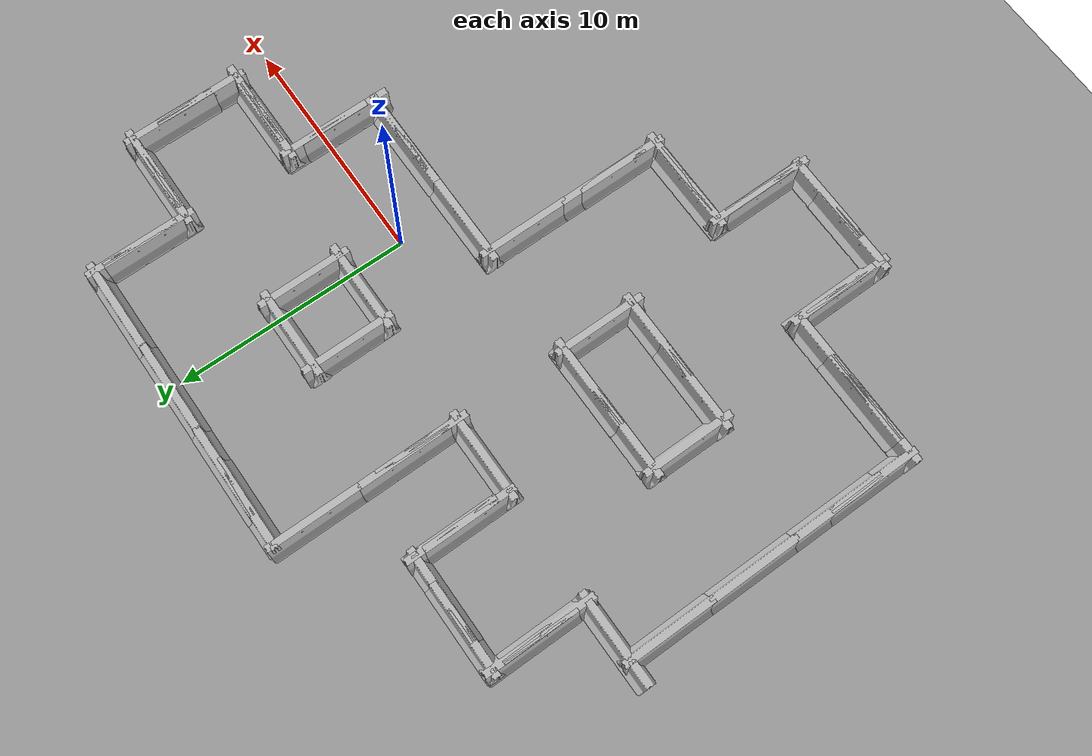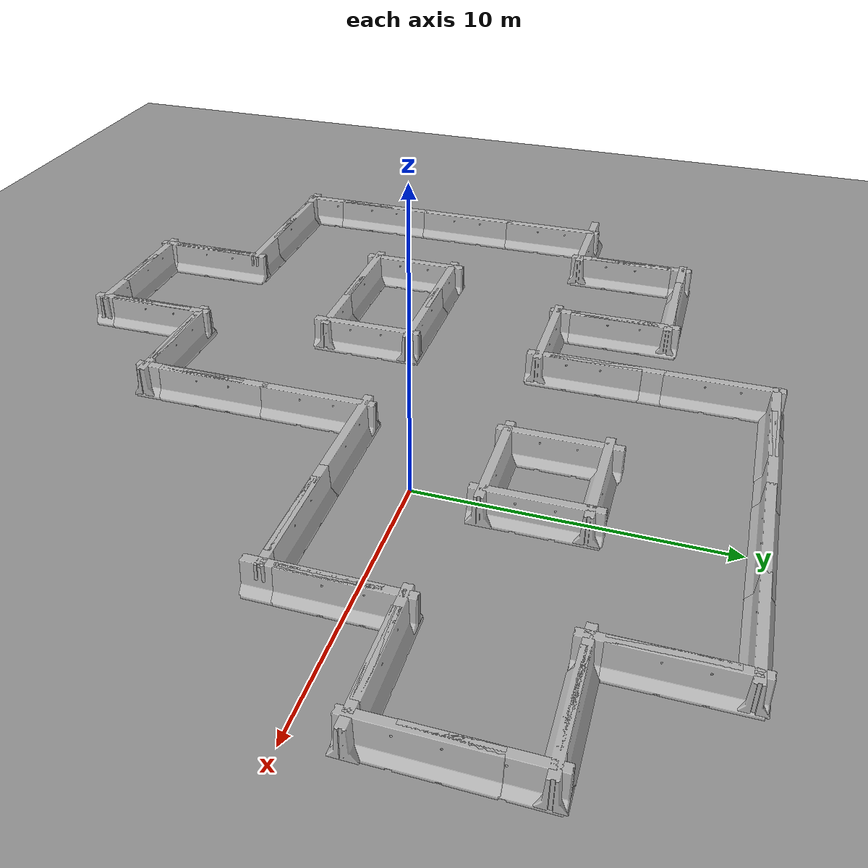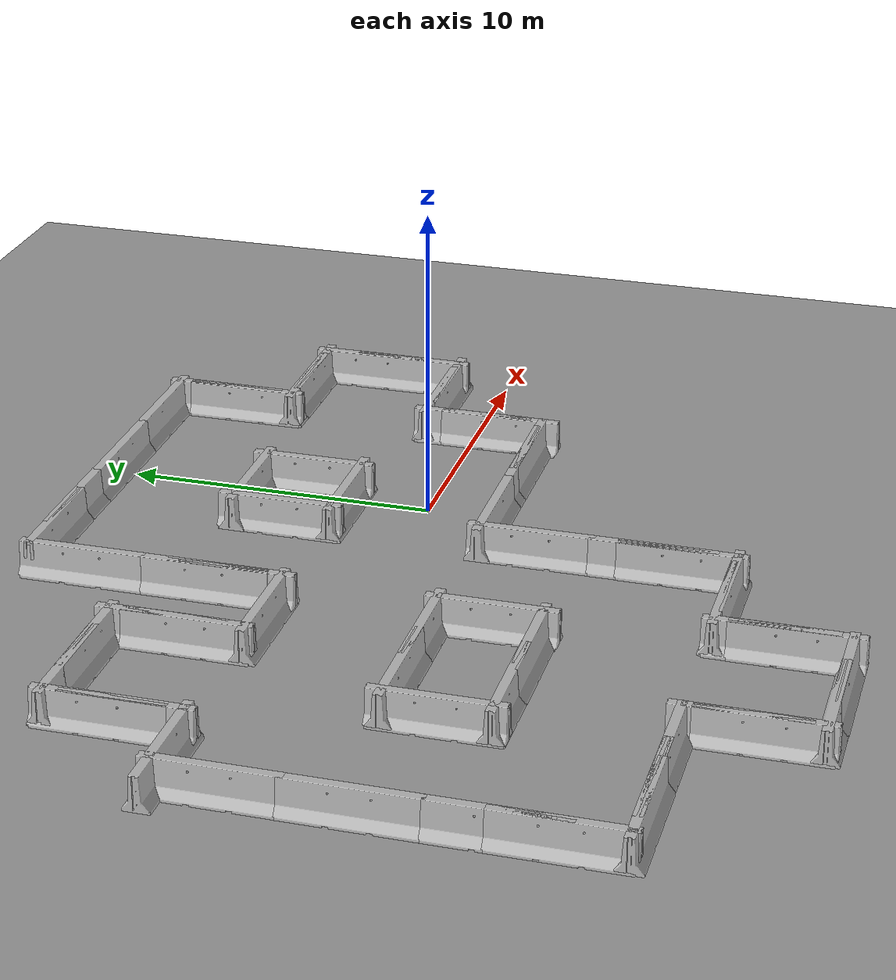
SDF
<sdf version="1.6">
 <world name="default">
  <light name="sun" type="directional">
   <pose>0 0 10 0 -0 0</pose>
   <diffuse>0.8 0.8 0.8 1</diffuse>
   <specular>0.2 0.2 0.2 1</specular>
   <attenuation>
    <range>1000</range>
    <constant>0.9</constant>
    <linear>0.01</linear>
    <quadratic>0.001</quadratic>
   </attenuation>
   <direction>0.5 0.1 -0.9</direction>
  </light>
  <scene><ambient>0.4 0.4 0.4 1</ambient><background>0.7 0.7 0.7 1</background><shadows>1</shadows></scene>
  <physics name="default_physics" default="0" type="ode">
   <max_step_size>0.01</max_step_size>
   <real_time_factor>1</real_time_factor>
   <real_time_update_rate>100</real_time_update_rate>
  </physics>
  <model name="ground_plane_0">
   <static>1</static>
   <link name="link">
    <collision name="collision">
     <geometry><plane><normal>0 0 1</normal><size>100 100</size></plane></geometry>
     <surface><friction><ode><mu>100</mu><mu2>50</mu2></ode></friction></surface>
    </collision>
    <visual name="visual">
     <cast_shadows>0</cast_shadows>
     <geometry><plane><normal>0 0 1</normal><size>100 100</size></plane></geometry>
     <material>
      <script><uri>file://media/materials/scripts/gazebo.material</uri><name>Gazebo/Grey</name></script>
     </material>
    </visual>
    <velocity_decay><linear>0</linear><angular>0</angular></velocity_decay>
   </link>
   <pose>0.497681 0 0 0 -0 0</pose>
  </model>
  <gravity>0 0 -9.8</gravity>
  <magnetic_field>6e-06 2.3e-05 -4.2e-05</magnetic_field>
  <atmosphere type="adiabatic"/>
  <spherical_coordinates>
   <surface_model>EARTH_WGS84</surface_model>
   <latitude_deg>0</latitude_deg>
   <longitude_deg>0</longitude_deg>
   <elevation>0</elevation>
   <heading_deg>0</heading_deg>
  </spherical_coordinates>
  <model name="jersey_barrier_0">
   <static>1</static>
   <link name="link">
    <visual name="visual">
     <geometry>
      <mesh><uri>model://jersey_barrier/meshes/jersey_barrier.dae</uri><scale>1 1 1</scale></mesh>
     </geometry>
    </visual>
    <collision name="upright">
     <pose>0 0 0.5715 0 -0 0</pose>
     <geometry><box><size>4.06542 0.3063 1.143</size></box></geometry>
    </collision>
    <collision name="base">
     <pose>0 0 0.032258 0 -0 0</pose>
     <geometry><box><size>4.06542 0.8107 0.064516</size></box></geometry>
    </collision>
    <collision name="base2">
     <pose>0 0 0.1 0 -0 0</pose>
     <geometry><box><size>4.06542 0.65 0.1</size></box></geometry>
    </collision>
    <collision name="base3">
     <pose>0 0 0.2 0 -0 0</pose>
     <geometry><box><size>4.06542 0.5 0.1</size></box></geometry>
    </collision>
    <collision name="left-angle">
     <pose>0 -0.224 0.2401 0.9 -0 0</pose>
     <geometry><box><size>4.06542 0.5 0.064516</size></box></geometry>
    </collision>
    <collision name="right-angle">
     <pose>0 0.224 0.2401 -0.9 0 0</pose>
     <geometry><box><size>4.06542 0.5 0.064516</size></box></geometry>
    </collision>
   </link>
   <pose>-1.02794 -2.40419 0 0 -0 0</pose>
  </model>
  <model name="jersey_barrier_0_clone">
   <static>1</static>
   <link name="link">
    <visual name="visual">
     <geometry>
      <mesh><uri>model://jersey_barrier/meshes/jersey_barrier.dae</uri><scale>1 1 1</scale></mesh>
     </geometry>
    </visual>
    <collision name="upright">
     <pose>0 0 0.5715 0 -0 0</pose>
     <geometry><box><size>4.06542 0.3063 1.143</size></box></geometry>
    </collision>
    <collision name="base">
     <pose>0 0 0.032258 0 -0 0</pose>
     <geometry><box><size>4.06542 0.8107 0.064516</size></box></geometry>
    </collision>
    <collision name="base2">
     <pose>0 0 0.1 0 -0 0</pose>
     <geometry><box><size>4.06542 0.65 0.1</size></box></geometry>
    </collision>
    <collision name="base3">
     <pose>0 0 0.2 0 -0 0</pose>
     <geometry><box><size>4.06542 0.5 0.1</size></box></geometry>
    </collision>
    <collision name="left-angle">
     <pose>0 -0.224 0.2401 0.9 -0 0</pose>
     <geometry><box><size>4.06542 0.5 0.064516</size></box></geometry>
    </collision>
    <collision name="right-angle">
     <pose>0 0.224 0.2401 -0.9 0 0</pose>
     <geometry><box><size>4.06542 0.5 0.064516</size></box></geometry>
    </collision>
   </link>
   <pose>-0.985005 2.41708 0 0 -0 0</pose>
  </model>
  <model name="jersey_barrier_0_clone_0">
   <static>1</static>
   <link name="link">
    <visual name="visual">
     <geometry>
      <mesh><uri>model://jersey_barrier/meshes/jersey_barrier.dae</uri><scale>1 1 1</scale></mesh>
     </geometry>
    </visual>
    <collision name="upright">
     <pose>0 0 0.5715 0 -0 0</pose>
     <geometry><box><size>4.06542 0.3063 1.143</size></box></geometry>
    </collision>
    <collision name="base">
     <pose>0 0 0.032258 0 -0 0</pose>
     <geometry><box><size>4.06542 0.8107 0.064516</size></box></geometry>
    </collision>
    <collision name="base2">
     <pose>0 0 0.1 0 -0 0</pose>
     <geometry><box><size>4.06542 0.65 0.1</size></box></geometry>
    </collision>
    <collision name="base3">
     <pose>0 0 0.2 0 -0 0</pose>
     <geometry><box><size>4.06542 0.5 0.1</size></box></geometry>
    </collision>
    <collision name="left-angle">
     <pose>0 -0.224 0.2401 0.9 -0 0</pose>
     <geometry><box><size>4.06542 0.5 0.064516</size></box></geometry>
    </collision>
    <collision name="right-angle">
     <pose>0 0.224 0.2401 -0.9 0 0</pose>
     <geometry><box><size>4.06542 0.5 0.064516</size></box></geometry>
    </collision>
   </link>
   <pose>2.97453 -2.40474 0 0 -0 0</pose>
  </model>
  <model name="jersey_barrier_0_clone_1">
   <static>1</static>
   <link name="link">
    <visual name="visual">
     <geometry>
      <mesh><uri>model://jersey_barrier/meshes/jersey_barrier.dae</uri><scale>1 1 1</scale></mesh>
     </geometry>
    </visual>
    <collision name="upright">
     <pose>0 0 0.5715 0 -0 0</pose>
     <geometry><box><size>4.06542 0.3063 1.143</size></box></geometry>
    </collision>
    <collision name="base">
     <pose>0 0 0.032258 0 -0 0</pose>
     <geometry><box><size>4.06542 0.8107 0.064516</size></box></geometry>
    </collision>
    <collision name="base2">
     <pose>0 0 0.1 0 -0 0</pose>
     <geometry><box><size>4.06542 0.65 0.1</size></box></geometry>
    </collision>
    <collision name="base3">
     <pose>0 0 0.2 0 -0 0</pose>
     <geometry><box><size>4.06542 0.5 0.1</size></box></geometry>
    </collision>
    <collision name="left-angle">
     <pose>0 -0.224 0.2401 0.9 -0 0</pose>
     <geometry><box><size>4.06542 0.5 0.064516</size></box></geometry>
    </collision>
    <collision name="right-angle">
     <pose>0 0.224 0.2401 -0.9 0 0</pose>
     <geometry><box><size>4.06542 0.5 0.064516</size></box></geometry>
    </collision>
   </link>
   <pose>-4.19882 -10.4385 0 0 -0 0</pose>
  </model>
  <model name="jersey_barrier_0_clone_2">
   <static>1</static>
   <link name="link">
    <visual name="visual">
     <geometry>
      <mesh><uri>model://jersey_barrier/meshes/jersey_barrier.dae</uri><scale>1 1 1</scale></mesh>
     </geometry>
    </visual>
    <collision name="upright">
     <pose>0 0 0.5715 0 -0 0</pose>
     <geometry><box><size>4.06542 0.3063 1.143</size></box></geometry>
    </collision>
    <collision name="base">
     <pose>0 0 0.032258 0 -0 0</pose>
     <geometry><box><size>4.06542 0.8107 0.064516</size></box></geometry>
    </collision>
    <collision name="base2">
     <pose>0 0 0.1 0 -0 0</pose>
     <geometry><box><size>4.06542 0.65 0.1</size></box></geometry>
    </collision>
    <collision name="base3">
     <pose>0 0 0.2 0 -0 0</pose>
     <geometry><box><size>4.06542 0.5 0.1</size></box></geometry>
    </collision>
    <collision name="left-angle">
     <pose>0 -0.224 0.2401 0.9 -0 0</pose>
     <geometry><box><size>4.06542 0.5 0.064516</size></box></geometry>
    </collision>
    <collision name="right-angle">
     <pose>0 0.224 0.2401 -0.9 0 0</pose>
     <geometry><box><size>4.06542 0.5 0.064516</size></box></geometry>
    </collision>
   </link>
   <pose>-2.56744 -7.85074 0 0 -0 1.57549</pose>
  </model>
  <model name="jersey_barrier_0_clone_2_clone">
   <static>1</static>
   <link name="link">
    <visual name="visual">
     <geometry>
      <mesh><uri>model://jersey_barrier/meshes/jersey_barrier.dae</uri><scale>1 1 1</scale></mesh>
     </geometry>
    </visual>
    <collision name="upright">
     <pose>0 0 0.5715 0 -0 0</pose>
     <geometry><box><size>4.06542 0.3063 1.143</size></box></geometry>
    </collision>
    <collision name="base">
     <pose>0 0 0.032258 0 -0 0</pose>
     <geometry><box><size>4.06542 0.8107 0.064516</size></box></geometry>
    </collision>
    <collision name="base2">
     <pose>0 0 0.1 0 -0 0</pose>
     <geometry><box><size>4.06542 0.65 0.1</size></box></geometry>
    </collision>
    <collision name="base3">
     <pose>0 0 0.2 0 -0 0</pose>
     <geometry><box><size>4.06542 0.5 0.1</size></box></geometry>
    </collision>
    <collision name="left-angle">
     <pose>0 -0.224 0.2401 0.9 -0 0</pose>
     <geometry><box><size>4.06542 0.5 0.064516</size></box></geometry>
    </collision>
    <collision name="right-angle">
     <pose>0 0.224 0.2401 -0.9 0 0</pose>
     <geometry><box><size>4.06542 0.5 0.064516</size></box></geometry>
    </collision>
   </link>
   <pose>0.560996 4.02797 0 0 -0 1.57549</pose>
  </model>
  <model name="jersey_barrier_0_clone_2_clone_0">
   <static>1</static>
   <link name="link">
    <visual name="visual">
     <geometry>
      <mesh><uri>model://jersey_barrier/meshes/jersey_barrier.dae</uri><scale>1 1 1</scale></mesh>
     </geometry>
    </visual>
    <collision name="upright">
     <pose>0 0 0.5715 0 -0 0</pose>
     <geometry><box><size>4.06542 0.3063 1.143</size></box></geometry>
    </collision>
    <collision name="base">
     <pose>0 0 0.032258 0 -0 0</pose>
     <geometry><box><size>4.06542 0.8107 0.064516</size></box></geometry>
    </collision>
    <collision name="base2">
     <pose>0 0 0.1 0 -0 0</pose>
     <geometry><box><size>4.06542 0.65 0.1</size></box></geometry>
    </collision>
    <collision name="base3">
     <pose>0 0 0.2 0 -0 0</pose>
     <geometry><box><size>4.06542 0.5 0.1</size></box></geometry>
    </collision>
    <collision name="left-angle">
     <pose>0 -0.224 0.2401 0.9 -0 0</pose>
     <geometry><box><size>4.06542 0.5 0.064516</size></box></geometry>
    </collision>
    <collision name="right-angle">
     <pose>0 0.224 0.2401 -0.9 0 0</pose>
     <geometry><box><size>4.06542 0.5 0.064516</size></box></geometry>
    </collision>
   </link>
   <pose>5.40975 -0.96421 0 0 -0 1.57549</pose>
  </model>
  <model name="jersey_barrier_0_clone_2_clone_3">
   <static>1</static>
   <link name="link">
    <visual name="visual">
     <geometry>
      <mesh><uri>model://jersey_barrier/meshes/jersey_barrier.dae</uri><scale>1 1 1</scale></mesh>
     </geometry>
    </visual>
    <collision name="upright">
     <pose>0 0 0.5715 0 -0 0</pose>
     <geometry><box><size>4.06542 0.3063 1.143</size></box></geometry>
    </collision>
    <collision name="base">
     <pose>0 0 0.032258 0 -0 0</pose>
     <geometry><box><size>4.06542 0.8107 0.064516</size></box></geometry>
    </collision>
    <collision name="base2">
     <pose>0 0 0.1 0 -0 0</pose>
     <geometry><box><size>4.06542 0.65 0.1</size></box></geometry>
    </collision>
    <collision name="base3">
     <pose>0 0 0.2 0 -0 0</pose>
     <geometry><box><size>4.06542 0.5 0.1</size></box></geometry>
    </collision>
    <collision name="left-angle">
     <pose>0 -0.224 0.2401 0.9 -0 0</pose>
     <geometry><box><size>4.06542 0.5 0.064516</size></box></geometry>
    </collision>
    <collision name="right-angle">
     <pose>0 0.224 0.2401 -0.9 0 0</pose>
     <geometry><box><size>4.06542 0.5 0.064516</size></box></geometry>
    </collision>
   </link>
   <pose>-7.43243 4.80244 0 0 -0 1.57549</pose>
  </model>
  <model name="jersey_barrier_0_clone_1_clone">
   <static>1</static>
   <link name="link">
    <visual name="visual">
     <geometry>
      <mesh><uri>model://jersey_barrier/meshes/jersey_barrier.dae</uri><scale>1 1 1</scale></mesh>
     </geometry>
    </visual>
    <collision name="upright">
     <pose>0 0 0.5715 0 -0 0</pose>
     <geometry><box><size>4.06542 0.3063 1.143</size></box></geometry>
    </collision>
    <collision name="base">
     <pose>0 0 0.032258 0 -0 0</pose>
     <geometry><box><size>4.06542 0.8107 0.064516</size></box></geometry>
    </collision>
    <collision name="base2">
     <pose>0 0 0.1 0 -0 0</pose>
     <geometry><box><size>4.06542 0.65 0.1</size></box></geometry>
    </collision>
    <collision name="base3">
     <pose>0 0 0.2 0 -0 0</pose>
     <geometry><box><size>4.06542 0.5 0.1</size></box></geometry>
    </collision>
    <collision name="left-angle">
     <pose>0 -0.224 0.2401 0.9 -0 0</pose>
     <geometry><box><size>4.06542 0.5 0.064516</size></box></geometry>
    </collision>
    <collision name="right-angle">
     <pose>0 0.224 0.2401 -0.9 0 0</pose>
     <geometry><box><size>4.06542 0.5 0.064516</size></box></geometry>
    </collision>
   </link>
   <pose>-1.05227 5.60536 0 0 -0 0</pose>
  </model>
  <model name="jersey_barrier_0_clone_2_clone_3_clone">
   <static>1</static>
   <link name="link">
    <visual name="visual">
     <geometry>
      <mesh><uri>model://jersey_barrier/meshes/jersey_barrier.dae</uri><scale>1 1 1</scale></mesh>
     </geometry>
    </visual>
    <collision name="upright">
     <pose>0 0 0.5715 0 -0 0</pose>
     <geometry><box><size>4.06542 0.3063 1.143</size></box></geometry>
    </collision>
    <collision name="base">
     <pose>0 0 0.032258 0 -0 0</pose>
     <geometry><box><size>4.06542 0.8107 0.064516</size></box></geometry>
    </collision>
    <collision name="base2">
     <pose>0 0 0.1 0 -0 0</pose>
     <geometry><box><size>4.06542 0.65 0.1</size></box></geometry>
    </collision>
    <collision name="base3">
     <pose>0 0 0.2 0 -0 0</pose>
     <geometry><box><size>4.06542 0.5 0.1</size></box></geometry>
    </collision>
    <collision name="left-angle">
     <pose>0 -0.224 0.2401 0.9 -0 0</pose>
     <geometry><box><size>4.06542 0.5 0.064516</size></box></geometry>
    </collision>
    <collision name="right-angle">
     <pose>0 0.224 0.2401 -0.9 0 0</pose>
     <geometry><box><size>4.06542 0.5 0.064516</size></box></geometry>
    </collision>
   </link>
   <pose>-2.59517 4.08417 0 0 -0 1.57549</pose>
  </model>
  <model name="jersey_barrier_0_clone_2_clone_3_clone_0">
   <static>1</static>
   <link name="link">
    <visual name="visual">
     <geometry>
      <mesh><uri>model://jersey_barrier/meshes/jersey_barrier.dae</uri><scale>1 1 1</scale></mesh>
     </geometry>
    </visual>
    <collision name="upright">
     <pose>0 0 0.5715 0 -0 0</pose>
     <geometry><box><size>4.06542 0.3063 1.143</size></box></geometry>
    </collision>
    <collision name="base">
     <pose>0 0 0.032258 0 -0 0</pose>
     <geometry><box><size>4.06542 0.8107 0.064516</size></box></geometry>
    </collision>
    <collision name="base2">
     <pose>0 0 0.1 0 -0 0</pose>
     <geometry><box><size>4.06542 0.65 0.1</size></box></geometry>
    </collision>
    <collision name="base3">
     <pose>0 0 0.2 0 -0 0</pose>
     <geometry><box><size>4.06542 0.5 0.1</size></box></geometry>
    </collision>
    <collision name="left-angle">
     <pose>0 -0.224 0.2401 0.9 -0 0</pose>
     <geometry><box><size>4.06542 0.5 0.064516</size></box></geometry>
    </collision>
    <collision name="right-angle">
     <pose>0 0.224 0.2401 -0.9 0 0</pose>
     <geometry><box><size>4.06542 0.5 0.064516</size></box></geometry>
    </collision>
   </link>
   <pose>5.37228 8.0404 0 0 -0 1.57549</pose>
  </model>
  <model name="jersey_barrier_0_clone_1_clone_0">
   <static>1</static>
   <link name="link">
    <visual name="visual">
     <geometry>
      <mesh><uri>model://jersey_barrier/meshes/jersey_barrier.dae</uri><scale>1 1 1</scale></mesh>
     </geometry>
    </visual>
    <collision name="upright">
     <pose>0 0 0.5715 0 -0 0</pose>
     <geometry><box><size>4.06542 0.3063 1.143</size></box></geometry>
    </collision>
    <collision name="base">
     <pose>0 0 0.032258 0 -0 0</pose>
     <geometry><box><size>4.06542 0.8107 0.064516</size></box></geometry>
    </collision>
    <collision name="base2">
     <pose>0 0 0.1 0 -0 0</pose>
     <geometry><box><size>4.06542 0.65 0.1</size></box></geometry>
    </collision>
    <collision name="base3">
     <pose>0 0 0.2 0 -0 0</pose>
     <geometry><box><size>4.06542 0.5 0.1</size></box></geometry>
    </collision>
    <collision name="left-angle">
     <pose>0 -0.224 0.2401 0.9 -0 0</pose>
     <geometry><box><size>4.06542 0.5 0.064516</size></box></geometry>
    </collision>
    <collision name="right-angle">
     <pose>0 0.224 0.2401 -0.9 0 0</pose>
     <geometry><box><size>4.06542 0.5 0.064516</size></box></geometry>
    </collision>
   </link>
   <pose>3.72097 10.4565 0 0 -0 0</pose>
  </model>
  <model name="jersey_barrier_0_clone_1_clone_1">
   <static>1</static>
   <link name="link">
    <visual name="visual">
     <geometry>
      <mesh><uri>model://jersey_barrier/meshes/jersey_barrier.dae</uri><scale>1 1 1</scale></mesh>
     </geometry>
    </visual>
    <collision name="upright">
     <pose>0 0 0.5715 0 -0 0</pose>
     <geometry><box><size>4.06542 0.3063 1.143</size></box></geometry>
    </collision>
    <collision name="base">
     <pose>0 0 0.032258 0 -0 0</pose>
     <geometry><box><size>4.06542 0.8107 0.064516</size></box></geometry>
    </collision>
    <collision name="base2">
     <pose>0 0 0.1 0 -0 0</pose>
     <geometry><box><size>4.06542 0.65 0.1</size></box></geometry>
    </collision>
    <collision name="base3">
     <pose>0 0 0.2 0 -0 0</pose>
     <geometry><box><size>4.06542 0.5 0.1</size></box></geometry>
    </collision>
    <collision name="left-angle">
     <pose>0 -0.224 0.2401 0.9 -0 0</pose>
     <geometry><box><size>4.06542 0.5 0.064516</size></box></geometry>
    </collision>
    <collision name="right-angle">
     <pose>0 0.224 0.2401 -0.9 0 0</pose>
     <geometry><box><size>4.06542 0.5 0.064516</size></box></geometry>
    </collision>
   </link>
   <pose>-0.226344 10.4493 0 0 -0 0</pose>
  </model>
  <model name="jersey_barrier_0_clone_1_clone_2">
   <static>1</static>
   <link name="link">
    <visual name="visual">
     <geometry>
      <mesh><uri>model://jersey_barrier/meshes/jersey_barrier.dae</uri><scale>1 1 1</scale></mesh>
     </geometry>
    </visual>
    <collision name="upright">
     <pose>0 0 0.5715 0 -0 0</pose>
     <geometry><box><size>4.06542 0.3063 1.143</size></box></geometry>
    </collision>
    <collision name="base">
     <pose>0 0 0.032258 0 -0 0</pose>
     <geometry><box><size>4.06542 0.8107 0.064516</size></box></geometry>
    </collision>
    <collision name="base2">
     <pose>0 0 0.1 0 -0 0</pose>
     <geometry><box><size>4.06542 0.65 0.1</size></box></geometry>
    </collision>
    <collision name="base3">
     <pose>0 0 0.2 0 -0 0</pose>
     <geometry><box><size>4.06542 0.5 0.1</size></box></geometry>
    </collision>
    <collision name="left-angle">
     <pose>0 -0.224 0.2401 0.9 -0 0</pose>
     <geometry><box><size>4.06542 0.5 0.064516</size></box></geometry>
    </collision>
    <collision name="right-angle">
     <pose>0 0.224 0.2401 -0.9 0 0</pose>
     <geometry><box><size>4.06542 0.5 0.064516</size></box></geometry>
    </collision>
   </link>
   <pose>-4.14371 10.4629 0 0 -0 0</pose>
  </model>
  <model name="jersey_barrier_0_clone_2_clone_3_clone_1">
   <static>1</static>
   <link name="link">
    <visual name="visual">
     <geometry>
      <mesh><uri>model://jersey_barrier/meshes/jersey_barrier.dae</uri><scale>1 1 1</scale></mesh>
     </geometry>
    </visual>
    <collision name="upright">
     <pose>0 0 0.5715 0 -0 0</pose>
     <geometry><box><size>4.06542 0.3063 1.143</size></box></geometry>
    </collision>
    <collision name="base">
     <pose>0 0 0.032258 0 -0 0</pose>
     <geometry><box><size>4.06542 0.8107 0.064516</size></box></geometry>
    </collision>
    <collision name="base2">
     <pose>0 0 0.1 0 -0 0</pose>
     <geometry><box><size>4.06542 0.65 0.1</size></box></geometry>
    </collision>
    <collision name="base3">
     <pose>0 0 0.2 0 -0 0</pose>
     <geometry><box><size>4.06542 0.5 0.1</size></box></geometry>
    </collision>
    <collision name="left-angle">
     <pose>0 -0.224 0.2401 0.9 -0 0</pose>
     <geometry><box><size>4.06542 0.5 0.064516</size></box></geometry>
    </collision>
    <collision name="right-angle">
     <pose>0 0.224 0.2401 -0.9 0 0</pose>
     <geometry><box><size>4.06542 0.5 0.064516</size></box></geometry>
    </collision>
   </link>
   <pose>-7.4465 8.73158 0 0 -0 1.57549</pose>
  </model>
  <model name="jersey_barrier_0_clone_3">
   <static>1</static>
   <link name="link">
    <visual name="visual">
     <geometry>
      <mesh><uri>model://jersey_barrier/meshes/jersey_barrier.dae</uri><scale>1 1 1</scale></mesh>
     </geometry>
    </visual>
    <collision name="upright">
     <pose>0 0 0.5715 0 -0 0</pose>
     <geometry><box><size>4.06542 0.3063 1.143</size></box></geometry>
    </collision>
    <collision name="base">
     <pose>0 0 0.032258 0 -0 0</pose>
     <geometry><box><size>4.06542 0.8107 0.064516</size></box></geometry>
    </collision>
    <collision name="base2">
     <pose>0 0 0.1 0 -0 0</pose>
     <geometry><box><size>4.06542 0.65 0.1</size></box></geometry>
    </collision>
    <collision name="base3">
     <pose>0 0 0.2 0 -0 0</pose>
     <geometry><box><size>4.06542 0.5 0.1</size></box></geometry>
    </collision>
    <collision name="left-angle">
     <pose>0 -0.224 0.2401 0.9 -0 0</pose>
     <geometry><box><size>4.06542 0.5 0.064516</size></box></geometry>
    </collision>
    <collision name="right-angle">
     <pose>0 0.224 0.2401 -0.9 0 0</pose>
     <geometry><box><size>4.06542 0.5 0.064516</size></box></geometry>
    </collision>
   </link>
   <pose>-5.61097 10.4434 0 0 -0 0</pose>
  </model>
  <model name="jersey_barrier_0_clone_1_clone_3">
   <static>1</static>
   <link name="link">
    <visual name="visual">
     <geometry>
      <mesh><uri>model://jersey_barrier/meshes/jersey_barrier.dae</uri><scale>1 1 1</scale></mesh>
     </geometry>
    </visual>
    <collision name="upright">
     <pose>0 0 0.5715 0 -0 0</pose>
     <geometry><box><size>4.06542 0.3063 1.143</size></box></geometry>
    </collision>
    <collision name="base">
     <pose>0 0 0.032258 0 -0 0</pose>
     <geometry><box><size>4.06542 0.8107 0.064516</size></box></geometry>
    </collision>
    <collision name="base2">
     <pose>0 0 0.1 0 -0 0</pose>
     <geometry><box><size>4.06542 0.65 0.1</size></box></geometry>
    </collision>
    <collision name="base3">
     <pose>0 0 0.2 0 -0 0</pose>
     <geometry><box><size>4.06542 0.5 0.1</size></box></geometry>
    </collision>
    <collision name="left-angle">
     <pose>0 -0.224 0.2401 0.9 -0 0</pose>
     <geometry><box><size>4.06542 0.5 0.064516</size></box></geometry>
    </collision>
    <collision name="right-angle">
     <pose>0 0.224 0.2401 -0.9 0 0</pose>
     <geometry><box><size>4.06542 0.5 0.064516</size></box></geometry>
    </collision>
   </link>
   <pose>3.57274 -2.41009 0 0 -0 0</pose>
  </model>
  <model name="jersey_barrier_0_clone_2_clone_3_clone_2">
   <static>1</static>
   <link name="link">
    <visual name="visual">
     <geometry>
      <mesh><uri>model://jersey_barrier/meshes/jersey_barrier.dae</uri><scale>1 1 1</scale></mesh>
     </geometry>
    </visual>
    <collision name="upright">
     <pose>0 0 0.5715 0 -0 0</pose>
     <geometry><box><size>4.06542 0.3063 1.143</size></box></geometry>
    </collision>
    <collision name="base">
     <pose>0 0 0.032258 0 -0 0</pose>
     <geometry><box><size>4.06542 0.8107 0.064516</size></box></geometry>
    </collision>
    <collision name="base2">
     <pose>0 0 0.1 0 -0 0</pose>
     <geometry><box><size>4.06542 0.65 0.1</size></box></geometry>
    </collision>
    <collision name="base3">
     <pose>0 0 0.2 0 -0 0</pose>
     <geometry><box><size>4.06542 0.5 0.1</size></box></geometry>
    </collision>
    <collision name="left-angle">
     <pose>0 -0.224 0.2401 0.9 -0 0</pose>
     <geometry><box><size>4.06542 0.5 0.064516</size></box></geometry>
    </collision>
    <collision name="right-angle">
     <pose>0 0.224 0.2401 -0.9 0 0</pose>
     <geometry><box><size>4.06542 0.5 0.064516</size></box></geometry>
    </collision>
   </link>
   <pose>5.37768 8.78365 0 0 -0 1.57549</pose>
  </model>
  <model name="jersey_barrier_0_clone_2_clone_3_clone_3">
   <static>1</static>
   <link name="link">
    <visual name="visual">
     <geometry>
      <mesh><uri>model://jersey_barrier/meshes/jersey_barrier.dae</uri><scale>1 1 1</scale></mesh>
     </geometry>
    </visual>
    <collision name="upright">
     <pose>0 0 0.5715 0 -0 0</pose>
     <geometry><box><size>4.06542 0.3063 1.143</size></box></geometry>
    </collision>
    <collision name="base">
     <pose>0 0 0.032258 0 -0 0</pose>
     <geometry><box><size>4.06542 0.8107 0.064516</size></box></geometry>
    </collision>
    <collision name="base2">
     <pose>0 0 0.1 0 -0 0</pose>
     <geometry><box><size>4.06542 0.65 0.1</size></box></geometry>
    </collision>
    <collision name="base3">
     <pose>0 0 0.2 0 -0 0</pose>
     <geometry><box><size>4.06542 0.5 0.1</size></box></geometry>
    </collision>
    <collision name="left-angle">
     <pose>0 -0.224 0.2401 0.9 -0 0</pose>
     <geometry><box><size>4.06542 0.5 0.064516</size></box></geometry>
    </collision>
    <collision name="right-angle">
     <pose>0 0.224 0.2401 -0.9 0 0</pose>
     <geometry><box><size>4.06542 0.5 0.064516</size></box></geometry>
    </collision>
   </link>
   <pose>-7.42195 3.99004 0 0 -0 1.57549</pose>
  </model>
  <model name="jersey_barrier_0_clone_1_clone_4">
   <static>1</static>
   <link name="link">
    <visual name="visual">
     <geometry>
      <mesh><uri>model://jersey_barrier/meshes/jersey_barrier.dae</uri><scale>1 1 1</scale></mesh>
     </geometry>
    </visual>
    <collision name="upright">
     <pose>0 0 0.5715 0 -0 0</pose>
     <geometry><box><size>4.06542 0.3063 1.143</size></box></geometry>
    </collision>
    <collision name="base">
     <pose>0 0 0.032258 0 -0 0</pose>
     <geometry><box><size>4.06542 0.8107 0.064516</size></box></geometry>
    </collision>
    <collision name="base2">
     <pose>0 0 0.1 0 -0 0</pose>
     <geometry><box><size>4.06542 0.65 0.1</size></box></geometry>
    </collision>
    <collision name="base3">
     <pose>0 0 0.2 0 -0 0</pose>
     <geometry><box><size>4.06542 0.5 0.1</size></box></geometry>
    </collision>
    <collision name="left-angle">
     <pose>0 -0.224 0.2401 0.9 -0 0</pose>
     <geometry><box><size>4.06542 0.5 0.064516</size></box></geometry>
    </collision>
    <collision name="right-angle">
     <pose>0 0.224 0.2401 -0.9 0 0</pose>
     <geometry><box><size>4.06542 0.5 0.064516</size></box></geometry>
    </collision>
   </link>
   <pose>-9.07746 2.38434 0 0 -0 0</pose>
  </model>
  <model name="jersey_barrier_0_clone_1_clone_5">
   <static>1</static>
   <link name="link">
    <visual name="visual">
     <geometry>
      <mesh><uri>model://jersey_barrier/meshes/jersey_barrier.dae</uri><scale>1 1 1</scale></mesh>
     </geometry>
    </visual>
    <collision name="upright">
     <pose>0 0 0.5715 0 -0 0</pose>
     <geometry><box><size>4.06542 0.3063 1.143</size></box></geometry>
    </collision>
    <collision name="base">
     <pose>0 0 0.032258 0 -0 0</pose>
     <geometry><box><size>4.06542 0.8107 0.064516</size></box></geometry>
    </collision>
    <collision name="base2">
     <pose>0 0 0.1 0 -0 0</pose>
     <geometry><box><size>4.06542 0.65 0.1</size></box></geometry>
    </collision>
    <collision name="base3">
     <pose>0 0 0.2 0 -0 0</pose>
     <geometry><box><size>4.06542 0.5 0.1</size></box></geometry>
    </collision>
    <collision name="left-angle">
     <pose>0 -0.224 0.2401 0.9 -0 0</pose>
     <geometry><box><size>4.06542 0.5 0.064516</size></box></geometry>
    </collision>
    <collision name="right-angle">
     <pose>0 0.224 0.2401 -0.9 0 0</pose>
     <geometry><box><size>4.06542 0.5 0.064516</size></box></geometry>
    </collision>
   </link>
   <pose>-9.04937 -2.41898 0 0 -0 0</pose>
  </model>
  <model name="jersey_barrier_0_clone_2_clone_4">
   <static>1</static>
   <link name="link">
    <visual name="visual">
     <geometry>
      <mesh><uri>model://jersey_barrier/meshes/jersey_barrier.dae</uri><scale>1 1 1</scale></mesh>
     </geometry>
    </visual>
    <collision name="upright">
     <pose>0 0 0.5715 0 -0 0</pose>
     <geometry><box><size>4.06542 0.3063 1.143</size></box></geometry>
    </collision>
    <collision name="base">
     <pose>0 0 0.032258 0 -0 0</pose>
     <geometry><box><size>4.06542 0.8107 0.064516</size></box></geometry>
    </collision>
    <collision name="base2">
     <pose>0 0 0.1 0 -0 0</pose>
     <geometry><box><size>4.06542 0.65 0.1</size></box></geometry>
    </collision>
    <collision name="base3">
     <pose>0 0 0.2 0 -0 0</pose>
     <geometry><box><size>4.06542 0.5 0.1</size></box></geometry>
    </collision>
    <collision name="left-angle">
     <pose>0 -0.224 0.2401 0.9 -0 0</pose>
     <geometry><box><size>4.06542 0.5 0.064516</size></box></geometry>
    </collision>
    <collision name="right-angle">
     <pose>0 0.224 0.2401 -0.9 0 0</pose>
     <geometry><box><size>4.06542 0.5 0.064516</size></box></geometry>
    </collision>
   </link>
   <pose>-7.44439 -4.07454 0 0 -0 1.57549</pose>
  </model>
  <model name="jersey_barrier_0_clone_2_clone_5">
   <static>1</static>
   <link name="link">
    <visual name="visual">
     <geometry>
      <mesh><uri>model://jersey_barrier/meshes/jersey_barrier.dae</uri><scale>1 1 1</scale></mesh>
     </geometry>
    </visual>
    <collision name="upright">
     <pose>0 0 0.5715 0 -0 0</pose>
     <geometry><box><size>4.06542 0.3063 1.143</size></box></geometry>
    </collision>
    <collision name="base">
     <pose>0 0 0.032258 0 -0 0</pose>
     <geometry><box><size>4.06542 0.8107 0.064516</size></box></geometry>
    </collision>
    <collision name="base2">
     <pose>0 0 0.1 0 -0 0</pose>
     <geometry><box><size>4.06542 0.65 0.1</size></box></geometry>
    </collision>
    <collision name="base3">
     <pose>0 0 0.2 0 -0 0</pose>
     <geometry><box><size>4.06542 0.5 0.1</size></box></geometry>
    </collision>
    <collision name="left-angle">
     <pose>0 -0.224 0.2401 0.9 -0 0</pose>
     <geometry><box><size>4.06542 0.5 0.064516</size></box></geometry>
    </collision>
    <collision name="right-angle">
     <pose>0 0.224 0.2401 -0.9 0 0</pose>
     <geometry><box><size>4.06542 0.5 0.064516</size></box></geometry>
    </collision>
   </link>
   <pose>-2.57606 -4.04265 0 0 -0 1.57549</pose>
  </model>
  <model name="jersey_barrier_0_clone_1_clone_7">
   <static>1</static>
   <link name="link">
    <visual name="visual">
     <geometry>
      <mesh><uri>model://jersey_barrier/meshes/jersey_barrier.dae</uri><scale>1 1 1</scale></mesh>
     </geometry>
    </visual>
    <collision name="upright">
     <pose>0 0 0.5715 0 -0 0</pose>
     <geometry><box><size>4.06542 0.3063 1.143</size></box></geometry>
    </collision>
    <collision name="base">
     <pose>0 0 0.032258 0 -0 0</pose>
     <geometry><box><size>4.06542 0.8107 0.064516</size></box></geometry>
    </collision>
    <collision name="base2">
     <pose>0 0 0.1 0 -0 0</pose>
     <geometry><box><size>4.06542 0.65 0.1</size></box></geometry>
    </collision>
    <collision name="base3">
     <pose>0 0 0.2 0 -0 0</pose>
     <geometry><box><size>4.06542 0.5 0.1</size></box></geometry>
    </collision>
    <collision name="left-angle">
     <pose>0 -0.224 0.2401 0.9 -0 0</pose>
     <geometry><box><size>4.06542 0.5 0.064516</size></box></geometry>
    </collision>
    <collision name="right-angle">
     <pose>0 0.224 0.2401 -0.9 0 0</pose>
     <geometry><box><size>4.06542 0.5 0.064516</size></box></geometry>
    </collision>
   </link>
   <pose>-11.4391 -2.42637 0 0 -0 0</pose>
  </model>
  <model name="jersey_barrier_0_clone_1_clone_8">
   <static>1</static>
   <link name="link">
    <visual name="visual">
     <geometry>
      <mesh><uri>model://jersey_barrier/meshes/jersey_barrier.dae</uri><scale>1 1 1</scale></mesh>
     </geometry>
    </visual>
    <collision name="upright">
     <pose>0 0 0.5715 0 -0 0</pose>
     <geometry><box><size>4.06542 0.3063 1.143</size></box></geometry>
    </collision>
    <collision name="base">
     <pose>0 0 0.032258 0 -0 0</pose>
     <geometry><box><size>4.06542 0.8107 0.064516</size></box></geometry>
    </collision>
    <collision name="base2">
     <pose>0 0 0.1 0 -0 0</pose>
     <geometry><box><size>4.06542 0.65 0.1</size></box></geometry>
    </collision>
    <collision name="base3">
     <pose>0 0 0.2 0 -0 0</pose>
     <geometry><box><size>4.06542 0.5 0.1</size></box></geometry>
    </collision>
    <collision name="left-angle">
     <pose>0 -0.224 0.2401 0.9 -0 0</pose>
     <geometry><box><size>4.06542 0.5 0.064516</size></box></geometry>
    </collision>
    <collision name="right-angle">
     <pose>0 0.224 0.2401 -0.9 0 0</pose>
     <geometry><box><size>4.06542 0.5 0.064516</size></box></geometry>
    </collision>
   </link>
   <pose>-9.07425 -5.61036 0 0 -0 0</pose>
  </model>
  <model name="jersey_barrier_0_clone_1_clone_10">
   <static>1</static>
   <link name="link">
    <visual name="visual">
     <geometry>
      <mesh><uri>model://jersey_barrier/meshes/jersey_barrier.dae</uri><scale>1 1 1</scale></mesh>
     </geometry>
    </visual>
    <collision name="upright">
     <pose>0 0 0.5715 0 -0 0</pose>
     <geometry><box><size>4.06542 0.3063 1.143</size></box></geometry>
    </collision>
    <collision name="base">
     <pose>0 0 0.032258 0 -0 0</pose>
     <geometry><box><size>4.06542 0.8107 0.064516</size></box></geometry>
    </collision>
    <collision name="base2">
     <pose>0 0 0.1 0 -0 0</pose>
     <geometry><box><size>4.06542 0.65 0.1</size></box></geometry>
    </collision>
    <collision name="base3">
     <pose>0 0 0.2 0 -0 0</pose>
     <geometry><box><size>4.06542 0.5 0.1</size></box></geometry>
    </collision>
    <collision name="left-angle">
     <pose>0 -0.224 0.2401 0.9 -0 0</pose>
     <geometry><box><size>4.06542 0.5 0.064516</size></box></geometry>
    </collision>
    <collision name="right-angle">
     <pose>0 0.224 0.2401 -0.9 0 0</pose>
     <geometry><box><size>4.06542 0.5 0.064516</size></box></geometry>
    </collision>
   </link>
   <pose>-11.4398 -5.59984 0 0 -0 0</pose>
  </model>
  <model name="jersey_barrier_0_clone_2_clone_4_clone">
   <static>1</static>
   <link name="link">
    <visual name="visual">
     <geometry>
      <mesh><uri>model://jersey_barrier/meshes/jersey_barrier.dae</uri><scale>1 1 1</scale></mesh>
     </geometry>
    </visual>
    <collision name="upright">
     <pose>0 0 0.5715 0 -0 0</pose>
     <geometry><box><size>4.06542 0.3063 1.143</size></box></geometry>
    </collision>
    <collision name="base">
     <pose>0 0 0.032258 0 -0 0</pose>
     <geometry><box><size>4.06542 0.8107 0.064516</size></box></geometry>
    </collision>
    <collision name="base2">
     <pose>0 0 0.1 0 -0 0</pose>
     <geometry><box><size>4.06542 0.65 0.1</size></box></geometry>
    </collision>
    <collision name="base3">
     <pose>0 0 0.2 0 -0 0</pose>
     <geometry><box><size>4.06542 0.5 0.1</size></box></geometry>
    </collision>
    <collision name="left-angle">
     <pose>0 -0.224 0.2401 0.9 -0 0</pose>
     <geometry><box><size>4.06542 0.5 0.064516</size></box></geometry>
    </collision>
    <collision name="right-angle">
     <pose>0 0.224 0.2401 -0.9 0 0</pose>
     <geometry><box><size>4.06542 0.5 0.064516</size></box></geometry>
    </collision>
   </link>
   <pose>-13.0271 -3.9955 0 0 -0 1.57549</pose>
  </model>
  <model name="jersey_barrier_0_clone_2_clone_6">
   <static>1</static>
   <link name="link">
    <visual name="visual">
     <geometry>
      <mesh><uri>model://jersey_barrier/meshes/jersey_barrier.dae</uri><scale>1 1 1</scale></mesh>
     </geometry>
    </visual>
    <collision name="upright">
     <pose>0 0 0.5715 0 -0 0</pose>
     <geometry><box><size>4.06542 0.3063 1.143</size></box></geometry>
    </collision>
    <collision name="base">
     <pose>0 0 0.032258 0 -0 0</pose>
     <geometry><box><size>4.06542 0.8107 0.064516</size></box></geometry>
    </collision>
    <collision name="base2">
     <pose>0 0 0.1 0 -0 0</pose>
     <geometry><box><size>4.06542 0.65 0.1</size></box></geometry>
    </collision>
    <collision name="base3">
     <pose>0 0 0.2 0 -0 0</pose>
     <geometry><box><size>4.06542 0.5 0.1</size></box></geometry>
    </collision>
    <collision name="left-angle">
     <pose>0 -0.224 0.2401 0.9 -0 0</pose>
     <geometry><box><size>4.06542 0.5 0.064516</size></box></geometry>
    </collision>
    <collision name="right-angle">
     <pose>0 0.224 0.2401 -0.9 0 0</pose>
     <geometry><box><size>4.06542 0.5 0.064516</size></box></geometry>
    </collision>
   </link>
   <pose>-2.58513 -8.74482 0 0 -0 1.57549</pose>
  </model>
  <model name="jersey_barrier_0_clone_1_clone_13">
   <static>1</static>
   <link name="link">
    <visual name="visual">
     <geometry>
      <mesh><uri>model://jersey_barrier/meshes/jersey_barrier.dae</uri><scale>1 1 1</scale></mesh>
     </geometry>
    </visual>
    <collision name="upright">
     <pose>0 0 0.5715 0 -0 0</pose>
     <geometry><box><size>4.06542 0.3063 1.143</size></box></geometry>
    </collision>
    <collision name="base">
     <pose>0 0 0.032258 0 -0 0</pose>
     <geometry><box><size>4.06542 0.8107 0.064516</size></box></geometry>
    </collision>
    <collision name="base2">
     <pose>0 0 0.1 0 -0 0</pose>
     <geometry><box><size>4.06542 0.65 0.1</size></box></geometry>
    </collision>
    <collision name="base3">
     <pose>0 0 0.2 0 -0 0</pose>
     <geometry><box><size>4.06542 0.5 0.1</size></box></geometry>
    </collision>
    <collision name="left-angle">
     <pose>0 -0.224 0.2401 0.9 -0 0</pose>
     <geometry><box><size>4.06542 0.5 0.064516</size></box></geometry>
    </collision>
    <collision name="right-angle">
     <pose>0 0.224 0.2401 -0.9 0 0</pose>
     <geometry><box><size>4.06542 0.5 0.064516</size></box></geometry>
    </collision>
   </link>
   <pose>-13.4424 -10.4614 0 0 -0 0</pose>
  </model>
  <model name="jersey_barrier_0_clone_1_clone_14">
   <static>1</static>
   <link name="link">
    <visual name="visual">
     <geometry>
      <mesh><uri>model://jersey_barrier/meshes/jersey_barrier.dae</uri><scale>1 1 1</scale></mesh>
     </geometry>
    </visual>
    <collision name="upright">
     <pose>0 0 0.5715 0 -0 0</pose>
     <geometry><box><size>4.06542 0.3063 1.143</size></box></geometry>
    </collision>
    <collision name="base">
     <pose>0 0 0.032258 0 -0 0</pose>
     <geometry><box><size>4.06542 0.8107 0.064516</size></box></geometry>
    </collision>
    <collision name="base2">
     <pose>0 0 0.1 0 -0 0</pose>
     <geometry><box><size>4.06542 0.65 0.1</size></box></geometry>
    </collision>
    <collision name="base3">
     <pose>0 0 0.2 0 -0 0</pose>
     <geometry><box><size>4.06542 0.5 0.1</size></box></geometry>
    </collision>
    <collision name="left-angle">
     <pose>0 -0.224 0.2401 0.9 -0 0</pose>
     <geometry><box><size>4.06542 0.5 0.064516</size></box></geometry>
    </collision>
    <collision name="right-angle">
     <pose>0 0.224 0.2401 -0.9 0 0</pose>
     <geometry><box><size>4.06542 0.5 0.064516</size></box></geometry>
    </collision>
   </link>
   <pose>-15.4018 -10.4601 0 0 -0 0</pose>
  </model>
  <model name="jersey_barrier_0_clone_2_clone_4_clone_clone">
   <static>1</static>
   <link name="link">
    <visual name="visual">
     <geometry>
      <mesh><uri>model://jersey_barrier/meshes/jersey_barrier.dae</uri><scale>1 1 1</scale></mesh>
     </geometry>
    </visual>
    <collision name="upright">
     <pose>0 0 0.5715 0 -0 0</pose>
     <geometry><box><size>4.06542 0.3063 1.143</size></box></geometry>
    </collision>
    <collision name="base">
     <pose>0 0 0.032258 0 -0 0</pose>
     <geometry><box><size>4.06542 0.8107 0.064516</size></box></geometry>
    </collision>
    <collision name="base2">
     <pose>0 0 0.1 0 -0 0</pose>
     <geometry><box><size>4.06542 0.65 0.1</size></box></geometry>
    </collision>
    <collision name="base3">
     <pose>0 0 0.2 0 -0 0</pose>
     <geometry><box><size>4.06542 0.5 0.1</size></box></geometry>
    </collision>
    <collision name="left-angle">
     <pose>0 -0.224 0.2401 0.9 -0 0</pose>
     <geometry><box><size>4.06542 0.5 0.064516</size></box></geometry>
    </collision>
    <collision name="right-angle">
     <pose>0 0.224 0.2401 -0.9 0 0</pose>
     <geometry><box><size>4.06542 0.5 0.064516</size></box></geometry>
    </collision>
   </link>
   <pose>-18.0345 0.68222 0 0 -0 1.57549</pose>
  </model>
  <model name="jersey_barrier_0_clone_2_clone_4_clone_clone_0">
   <static>1</static>
   <link name="link">
    <visual name="visual">
     <geometry>
      <mesh><uri>model://jersey_barrier/meshes/jersey_barrier.dae</uri><scale>1 1 1</scale></mesh>
     </geometry>
    </visual>
    <collision name="upright">
     <pose>0 0 0.5715 0 -0 0</pose>
     <geometry><box><size>4.06542 0.3063 1.143</size></box></geometry>
    </collision>
    <collision name="base">
     <pose>0 0 0.032258 0 -0 0</pose>
     <geometry><box><size>4.06542 0.8107 0.064516</size></box></geometry>
    </collision>
    <collision name="base2">
     <pose>0 0 0.1 0 -0 0</pose>
     <geometry><box><size>4.06542 0.65 0.1</size></box></geometry>
    </collision>
    <collision name="base3">
     <pose>0 0 0.2 0 -0 0</pose>
     <geometry><box><size>4.06542 0.5 0.1</size></box></geometry>
    </collision>
    <collision name="left-angle">
     <pose>0 -0.224 0.2401 0.9 -0 0</pose>
     <geometry><box><size>4.06542 0.5 0.064516</size></box></geometry>
    </collision>
    <collision name="right-angle">
     <pose>0 0.224 0.2401 -0.9 0 0</pose>
     <geometry><box><size>4.06542 0.5 0.064516</size></box></geometry>
    </collision>
   </link>
   <pose>-18.0231 -3.12239 0 0 -0 1.57549</pose>
  </model>
  <model name="jersey_barrier_0_clone_2_clone_4_clone_clone_1">
   <static>1</static>
   <link name="link">
    <visual name="visual">
     <geometry>
      <mesh><uri>model://jersey_barrier/meshes/jersey_barrier.dae</uri><scale>1 1 1</scale></mesh>
     </geometry>
    </visual>
    <collision name="upright">
     <pose>0 0 0.5715 0 -0 0</pose>
     <geometry><box><size>4.06542 0.3063 1.143</size></box></geometry>
    </collision>
    <collision name="base">
     <pose>0 0 0.032258 0 -0 0</pose>
     <geometry><box><size>4.06542 0.8107 0.064516</size></box></geometry>
    </collision>
    <collision name="base2">
     <pose>0 0 0.1 0 -0 0</pose>
     <geometry><box><size>4.06542 0.65 0.1</size></box></geometry>
    </collision>
    <collision name="base3">
     <pose>0 0 0.2 0 -0 0</pose>
     <geometry><box><size>4.06542 0.5 0.1</size></box></geometry>
    </collision>
    <collision name="left-angle">
     <pose>0 -0.224 0.2401 0.9 -0 0</pose>
     <geometry><box><size>4.06542 0.5 0.064516</size></box></geometry>
    </collision>
    <collision name="right-angle">
     <pose>0 0.224 0.2401 -0.9 0 0</pose>
     <geometry><box><size>4.06542 0.5 0.064516</size></box></geometry>
    </collision>
   </link>
   <pose>-18.0062 -7.01659 0 0 -0 1.57549</pose>
  </model>
  <model name="jersey_barrier_0_clone_2_clone_4_clone_clone_2">
   <static>1</static>
   <link name="link">
    <visual name="visual">
     <geometry>
      <mesh><uri>model://jersey_barrier/meshes/jersey_barrier.dae</uri><scale>1 1 1</scale></mesh>
     </geometry>
    </visual>
    <collision name="upright">
     <pose>0 0 0.5715 0 -0 0</pose>
     <geometry><box><size>4.06542 0.3063 1.143</size></box></geometry>
    </collision>
    <collision name="base">
     <pose>0 0 0.032258 0 -0 0</pose>
     <geometry><box><size>4.06542 0.8107 0.064516</size></box></geometry>
    </collision>
    <collision name="base2">
     <pose>0 0 0.1 0 -0 0</pose>
     <geometry><box><size>4.06542 0.65 0.1</size></box></geometry>
    </collision>
    <collision name="base3">
     <pose>0 0 0.2 0 -0 0</pose>
     <geometry><box><size>4.06542 0.5 0.1</size></box></geometry>
    </collision>
    <collision name="left-angle">
     <pose>0 -0.224 0.2401 0.9 -0 0</pose>
     <geometry><box><size>4.06542 0.5 0.064516</size></box></geometry>
    </collision>
    <collision name="right-angle">
     <pose>0 0.224 0.2401 -0.9 0 0</pose>
     <geometry><box><size>4.06542 0.5 0.064516</size></box></geometry>
    </collision>
   </link>
   <pose>-17.9989 -8.67248 0 0 -0 1.57549</pose>
  </model>
  <model name="jersey_barrier_0_clone_1_clone_14_clone">
   <static>1</static>
   <link name="link">
    <visual name="visual">
     <geometry>
      <mesh><uri>model://jersey_barrier/meshes/jersey_barrier.dae</uri><scale>1 1 1</scale></mesh>
     </geometry>
    </visual>
    <collision name="upright">
     <pose>0 0 0.5715 0 -0 0</pose>
     <geometry><box><size>4.06542 0.3063 1.143</size></box></geometry>
    </collision>
    <collision name="base">
     <pose>0 0 0.032258 0 -0 0</pose>
     <geometry><box><size>4.06542 0.8107 0.064516</size></box></geometry>
    </collision>
    <collision name="base2">
     <pose>0 0 0.1 0 -0 0</pose>
     <geometry><box><size>4.06542 0.65 0.1</size></box></geometry>
    </collision>
    <collision name="base3">
     <pose>0 0 0.2 0 -0 0</pose>
     <geometry><box><size>4.06542 0.5 0.1</size></box></geometry>
    </collision>
    <collision name="left-angle">
     <pose>0 -0.224 0.2401 0.9 -0 0</pose>
     <geometry><box><size>4.06542 0.5 0.064516</size></box></geometry>
    </collision>
    <collision name="right-angle">
     <pose>0 0.224 0.2401 -0.9 0 0</pose>
     <geometry><box><size>4.06542 0.5 0.064516</size></box></geometry>
    </collision>
   </link>
   <pose>-16.3909 -10.4718 0 0 -0 0</pose>
  </model>
  <model name="jersey_barrier_0_clone_4">
   <static>1</static>
   <link name="link">
    <visual name="visual">
     <geometry>
      <mesh><uri>model://jersey_barrier/meshes/jersey_barrier.dae</uri><scale>1 1 1</scale></mesh>
     </geometry>
    </visual>
    <collision name="upright">
     <pose>0 0 0.5715 0 -0 0</pose>
     <geometry><box><size>4.06542 0.3063 1.143</size></box></geometry>
    </collision>
    <collision name="base">
     <pose>0 0 0.032258 0 -0 0</pose>
     <geometry><box><size>4.06542 0.8107 0.064516</size></box></geometry>
    </collision>
    <collision name="base2">
     <pose>0 0 0.1 0 -0 0</pose>
     <geometry><box><size>4.06542 0.65 0.1</size></box></geometry>
    </collision>
    <collision name="base3">
     <pose>0 0 0.2 0 -0 0</pose>
     <geometry><box><size>4.06542 0.5 0.1</size></box></geometry>
    </collision>
    <collision name="left-angle">
     <pose>0 -0.224 0.2401 0.9 -0 0</pose>
     <geometry><box><size>4.06542 0.5 0.064516</size></box></geometry>
    </collision>
    <collision name="right-angle">
     <pose>0 0.224 0.2401 -0.9 0 0</pose>
     <geometry><box><size>4.06542 0.5 0.064516</size></box></geometry>
    </collision>
   </link>
   <pose>7.04924 1.61521 0 0 -0 0</pose>
  </model>
  <model name="jersey_barrier_0_clone_5">
   <static>1</static>
   <link name="link">
    <visual name="visual">
     <geometry>
      <mesh><uri>model://jersey_barrier/meshes/jersey_barrier.dae</uri><scale>1 1 1</scale></mesh>
     </geometry>
    </visual>
    <collision name="upright">
     <pose>0 0 0.5715 0 -0 0</pose>
     <geometry><box><size>4.06542 0.3063 1.143</size></box></geometry>
    </collision>
    <collision name="base">
     <pose>0 0 0.032258 0 -0 0</pose>
     <geometry><box><size>4.06542 0.8107 0.064516</size></box></geometry>
    </collision>
    <collision name="base2">
     <pose>0 0 0.1 0 -0 0</pose>
     <geometry><box><size>4.06542 0.65 0.1</size></box></geometry>
    </collision>
    <collision name="base3">
     <pose>0 0 0.2 0 -0 0</pose>
     <geometry><box><size>4.06542 0.5 0.1</size></box></geometry>
    </collision>
    <collision name="left-angle">
     <pose>0 -0.224 0.2401 0.9 -0 0</pose>
     <geometry><box><size>4.06542 0.5 0.064516</size></box></geometry>
    </collision>
    <collision name="right-angle">
     <pose>0 0.224 0.2401 -0.9 0 0</pose>
     <geometry><box><size>4.06542 0.5 0.064516</size></box></geometry>
    </collision>
   </link>
   <pose>6.9975 6.39661 0 0 -0 0</pose>
  </model>
  <model name="jersey_barrier_0_clone_2_clone_0_clone">
   <static>1</static>
   <link name="link">
    <visual name="visual">
     <geometry>
      <mesh><uri>model://jersey_barrier/meshes/jersey_barrier.dae</uri><scale>1 1 1</scale></mesh>
     </geometry>
    </visual>
    <collision name="upright">
     <pose>0 0 0.5715 0 -0 0</pose>
     <geometry><box><size>4.06542 0.3063 1.143</size></box></geometry>
    </collision>
    <collision name="base">
     <pose>0 0 0.032258 0 -0 0</pose>
     <geometry><box><size>4.06542 0.8107 0.064516</size></box></geometry>
    </collision>
    <collision name="base2">
     <pose>0 0 0.1 0 -0 0</pose>
     <geometry><box><size>4.06542 0.65 0.1</size></box></geometry>
    </collision>
    <collision name="base3">
     <pose>0 0 0.2 0 -0 0</pose>
     <geometry><box><size>4.06542 0.5 0.1</size></box></geometry>
    </collision>
    <collision name="left-angle">
     <pose>0 -0.224 0.2401 0.9 -0 0</pose>
     <geometry><box><size>4.06542 0.5 0.064516</size></box></geometry>
    </collision>
    <collision name="right-angle">
     <pose>0 0.224 0.2401 -0.9 0 0</pose>
     <geometry><box><size>4.06542 0.5 0.064516</size></box></geometry>
    </collision>
   </link>
   <pose>5.41249 -0.032329 0 0 -0 1.57549</pose>
  </model>
  <model name="jersey_barrier_0_clone_2_clone_0_clone_0">
   <static>1</static>
   <link name="link">
    <visual name="visual">
     <geometry>
      <mesh><uri>model://jersey_barrier/meshes/jersey_barrier.dae</uri><scale>1 1 1</scale></mesh>
     </geometry>
    </visual>
    <collision name="upright">
     <pose>0 0 0.5715 0 -0 0</pose>
     <geometry><box><size>4.06542 0.3063 1.143</size></box></geometry>
    </collision>
    <collision name="base">
     <pose>0 0 0.032258 0 -0 0</pose>
     <geometry><box><size>4.06542 0.8107 0.064516</size></box></geometry>
    </collision>
    <collision name="base2">
     <pose>0 0 0.1 0 -0 0</pose>
     <geometry><box><size>4.06542 0.65 0.1</size></box></geometry>
    </collision>
    <collision name="base3">
     <pose>0 0 0.2 0 -0 0</pose>
     <geometry><box><size>4.06542 0.5 0.1</size></box></geometry>
    </collision>
    <collision name="left-angle">
     <pose>0 -0.224 0.2401 0.9 -0 0</pose>
     <geometry><box><size>4.06542 0.5 0.064516</size></box></geometry>
    </collision>
    <collision name="right-angle">
     <pose>0 0.224 0.2401 -0.9 0 0</pose>
     <geometry><box><size>4.06542 0.5 0.064516</size></box></geometry>
    </collision>
   </link>
   <pose>9.41093 3.25851 0 0 -0 1.57549</pose>
  </model>
  <model name="jersey_barrier_0_clone_2_clone_0_clone_1">
   <static>1</static>
   <link name="link">
    <visual name="visual">
     <geometry>
      <mesh><uri>model://jersey_barrier/meshes/jersey_barrier.dae</uri><scale>1 1 1</scale></mesh>
     </geometry>
    </visual>
    <collision name="upright">
     <pose>0 0 0.5715 0 -0 0</pose>
     <geometry><box><size>4.06542 0.3063 1.143</size></box></geometry>
    </collision>
    <collision name="base">
     <pose>0 0 0.032258 0 -0 0</pose>
     <geometry><box><size>4.06542 0.8107 0.064516</size></box></geometry>
    </collision>
    <collision name="base2">
     <pose>0 0 0.1 0 -0 0</pose>
     <geometry><box><size>4.06542 0.65 0.1</size></box></geometry>
    </collision>
    <collision name="base3">
     <pose>0 0 0.2 0 -0 0</pose>
     <geometry><box><size>4.06542 0.5 0.1</size></box></geometry>
    </collision>
    <collision name="left-angle">
     <pose>0 -0.224 0.2401 0.9 -0 0</pose>
     <geometry><box><size>4.06542 0.5 0.064516</size></box></geometry>
    </collision>
    <collision name="right-angle">
     <pose>0 0.224 0.2401 -0.9 0 0</pose>
     <geometry><box><size>4.06542 0.5 0.064516</size></box></geometry>
    </collision>
   </link>
   <pose>9.39212 4.73145 0 0 -0 1.57549</pose>
  </model>
  <model name="jersey_barrier_0_clone_5_clone">
   <static>1</static>
   <link name="link">
    <visual name="visual">
     <geometry>
      <mesh><uri>model://jersey_barrier/meshes/jersey_barrier.dae</uri><scale>1 1 1</scale></mesh>
     </geometry>
    </visual>
    <collision name="upright">
     <pose>0 0 0.5715 0 -0 0</pose>
     <geometry><box><size>4.06542 0.3063 1.143</size></box></geometry>
    </collision>
    <collision name="base">
     <pose>0 0 0.032258 0 -0 0</pose>
     <geometry><box><size>4.06542 0.8107 0.064516</size></box></geometry>
    </collision>
    <collision name="base2">
     <pose>0 0 0.1 0 -0 0</pose>
     <geometry><box><size>4.06542 0.65 0.1</size></box></geometry>
    </collision>
    <collision name="base3">
     <pose>0 0 0.2 0 -0 0</pose>
     <geometry><box><size>4.06542 0.5 0.1</size></box></geometry>
    </collision>
    <collision name="left-angle">
     <pose>0 -0.224 0.2401 0.9 -0 0</pose>
     <geometry><box><size>4.06542 0.5 0.064516</size></box></geometry>
    </collision>
    <collision name="right-angle">
     <pose>0 0.224 0.2401 -0.9 0 0</pose>
     <geometry><box><size>4.06542 0.5 0.064516</size></box></geometry>
    </collision>
   </link>
   <pose>7.77238 6.38245 0 0 -0 0</pose>
  </model>
  <model name="jersey_barrier_0_clone_5_clone_0">
   <static>1</static>
   <link name="link">
    <visual name="visual">
     <geometry>
      <mesh><uri>model://jersey_barrier/meshes/jersey_barrier.dae</uri><scale>1 1 1</scale></mesh>
     </geometry>
    </visual>
    <collision name="upright">
     <pose>0 0 0.5715 0 -0 0</pose>
     <geometry><box><size>4.06542 0.3063 1.143</size></box></geometry>
    </collision>
    <collision name="base">
     <pose>0 0 0.032258 0 -0 0</pose>
     <geometry><box><size>4.06542 0.8107 0.064516</size></box></geometry>
    </collision>
    <collision name="base2">
     <pose>0 0 0.1 0 -0 0</pose>
     <geometry><box><size>4.06542 0.65 0.1</size></box></geometry>
    </collision>
    <collision name="base3">
     <pose>0 0 0.2 0 -0 0</pose>
     <geometry><box><size>4.06542 0.5 0.1</size></box></geometry>
    </collision>
    <collision name="left-angle">
     <pose>0 -0.224 0.2401 0.9 -0 0</pose>
     <geometry><box><size>4.06542 0.5 0.064516</size></box></geometry>
    </collision>
    <collision name="right-angle">
     <pose>0 0.224 0.2401 -0.9 0 0</pose>
     <geometry><box><size>4.06542 0.5 0.064516</size></box></geometry>
    </collision>
   </link>
   <pose>7.90888 1.57973 0 0 -0 0</pose>
  </model>
  <model name="jersey_barrier_0_clone_2_clone_6_clone">
   <static>1</static>
   <link name="link">
    <visual name="visual">
     <geometry>
      <mesh><uri>model://jersey_barrier/meshes/jersey_barrier.dae</uri><scale>1 1 1</scale></mesh>
     </geometry>
    </visual>
    <collision name="upright">
     <pose>0 0 0.5715 0 -0 0</pose>
     <geometry><box><size>4.06542 0.3063 1.143</size></box></geometry>
    </collision>
    <collision name="base">
     <pose>0 0 0.032258 0 -0 0</pose>
     <geometry><box><size>4.06542 0.8107 0.064516</size></box></geometry>
    </collision>
    <collision name="base2">
     <pose>0 0 0.1 0 -0 0</pose>
     <geometry><box><size>4.06542 0.65 0.1</size></box></geometry>
    </collision>
    <collision name="base3">
     <pose>0 0 0.2 0 -0 0</pose>
     <geometry><box><size>4.06542 0.5 0.1</size></box></geometry>
    </collision>
    <collision name="left-angle">
     <pose>0 -0.224 0.2401 0.9 -0 0</pose>
     <geometry><box><size>4.06542 0.5 0.064516</size></box></geometry>
    </collision>
    <collision name="right-angle">
     <pose>0 0.224 0.2401 -0.9 0 0</pose>
     <geometry><box><size>4.06542 0.5 0.064516</size></box></geometry>
    </collision>
   </link>
   <pose>-11.5824 -12.0812 0 0 -0 1.57549</pose>
  </model>
  <model name="jersey_barrier_0_clone_2_clone_6_clone_0">
   <static>1</static>
   <link name="link">
    <visual name="visual">
     <geometry>
      <mesh><uri>model://jersey_barrier/meshes/jersey_barrier.dae</uri><scale>1 1 1</scale></mesh>
     </geometry>
    </visual>
    <collision name="upright">
     <pose>0 0 0.5715 0 -0 0</pose>
     <geometry><box><size>4.06542 0.3063 1.143</size></box></geometry>
    </collision>
    <collision name="base">
     <pose>0 0 0.032258 0 -0 0</pose>
     <geometry><box><size>4.06542 0.8107 0.064516</size></box></geometry>
    </collision>
    <collision name="base2">
     <pose>0 0 0.1 0 -0 0</pose>
     <geometry><box><size>4.06542 0.65 0.1</size></box></geometry>
    </collision>
    <collision name="base3">
     <pose>0 0 0.2 0 -0 0</pose>
     <geometry><box><size>4.06542 0.5 0.1</size></box></geometry>
    </collision>
    <collision name="left-angle">
     <pose>0 -0.224 0.2401 0.9 -0 0</pose>
     <geometry><box><size>4.06542 0.5 0.064516</size></box></geometry>
    </collision>
    <collision name="right-angle">
     <pose>0 0.224 0.2401 -0.9 0 0</pose>
     <geometry><box><size>4.06542 0.5 0.064516</size></box></geometry>
    </collision>
   </link>
   <pose>-6.57792 -12.1068 0 0 -0 1.57549</pose>
  </model>
  <model name="jersey_barrier_0_clone_1_clone_11">
   <static>1</static>
   <link name="link">
    <visual name="visual">
     <geometry>
      <mesh><uri>model://jersey_barrier/meshes/jersey_barrier.dae</uri><scale>1 1 1</scale></mesh>
     </geometry>
    </visual>
    <collision name="upright">
     <pose>0 0 0.5715 0 -0 0</pose>
     <geometry><box><size>4.06542 0.3063 1.143</size></box></geometry>
    </collision>
    <collision name="base">
     <pose>0 0 0.032258 0 -0 0</pose>
     <geometry><box><size>4.06542 0.8107 0.064516</size></box></geometry>
    </collision>
    <collision name="base2">
     <pose>0 0 0.1 0 -0 0</pose>
     <geometry><box><size>4.06542 0.65 0.1</size></box></geometry>
    </collision>
    <collision name="base3">
     <pose>0 0 0.2 0 -0 0</pose>
     <geometry><box><size>4.06542 0.5 0.1</size></box></geometry>
    </collision>
    <collision name="left-angle">
     <pose>0 -0.224 0.2401 0.9 -0 0</pose>
     <geometry><box><size>4.06542 0.5 0.064516</size></box></geometry>
    </collision>
    <collision name="right-angle">
     <pose>0 0.224 0.2401 -0.9 0 0</pose>
     <geometry><box><size>4.06542 0.5 0.064516</size></box></geometry>
    </collision>
   </link>
   <pose>-4.93294 -10.426 0 0 -0 0</pose>
  </model>
  <model name="jersey_barrier_0_clone_1_clone_12">
   <static>1</static>
   <link name="link">
    <visual name="visual">
     <geometry>
      <mesh><uri>model://jersey_barrier/meshes/jersey_barrier.dae</uri><scale>1 1 1</scale></mesh>
     </geometry>
    </visual>
    <collision name="upright">
     <pose>0 0 0.5715 0 -0 0</pose>
     <geometry><box><size>4.06542 0.3063 1.143</size></box></geometry>
    </collision>
    <collision name="base">
     <pose>0 0 0.032258 0 -0 0</pose>
     <geometry><box><size>4.06542 0.8107 0.064516</size></box></geometry>
    </collision>
    <collision name="base2">
     <pose>0 0 0.1 0 -0 0</pose>
     <geometry><box><size>4.06542 0.65 0.1</size></box></geometry>
    </collision>
    <collision name="base3">
     <pose>0 0 0.2 0 -0 0</pose>
     <geometry><box><size>4.06542 0.5 0.1</size></box></geometry>
    </collision>
    <collision name="left-angle">
     <pose>0 -0.224 0.2401 0.9 -0 0</pose>
     <geometry><box><size>4.06542 0.5 0.064516</size></box></geometry>
    </collision>
    <collision name="right-angle">
     <pose>0 0.224 0.2401 -0.9 0 0</pose>
     <geometry><box><size>4.06542 0.5 0.064516</size></box></geometry>
    </collision>
   </link>
   <pose>-8.35557 -14.4512 0 0 -0 0</pose>
  </model>
  <model name="jersey_barrier_0_clone_1_clone_15">
   <static>1</static>
   <link name="link">
    <visual name="visual">
     <geometry>
      <mesh><uri>model://jersey_barrier/meshes/jersey_barrier.dae</uri><scale>1 1 1</scale></mesh>
     </geometry>
    </visual>
    <collision name="upright">
     <pose>0 0 0.5715 0 -0 0</pose>
     <geometry><box><size>4.06542 0.3063 1.143</size></box></geometry>
    </collision>
    <collision name="base">
     <pose>0 0 0.032258 0 -0 0</pose>
     <geometry><box><size>4.06542 0.8107 0.064516</size></box></geometry>
    </collision>
    <collision name="base2">
     <pose>0 0 0.1 0 -0 0</pose>
     <geometry><box><size>4.06542 0.65 0.1</size></box></geometry>
    </collision>
    <collision name="base3">
     <pose>0 0 0.2 0 -0 0</pose>
     <geometry><box><size>4.06542 0.5 0.1</size></box></geometry>
    </collision>
    <collision name="left-angle">
     <pose>0 -0.224 0.2401 0.9 -0 0</pose>
     <geometry><box><size>4.06542 0.5 0.064516</size></box></geometry>
    </collision>
    <collision name="right-angle">
     <pose>0 0.224 0.2401 -0.9 0 0</pose>
     <geometry><box><size>4.06542 0.5 0.064516</size></box></geometry>
    </collision>
   </link>
   <pose>-9.96065 -14.4391 0 0 -0 0</pose>
  </model>
  <model name="jersey_barrier_0_clone_2_clone_6_clone_clone">
   <static>1</static>
   <link name="link">
    <visual name="visual">
     <geometry>
      <mesh><uri>model://jersey_barrier/meshes/jersey_barrier.dae</uri><scale>1 1 1</scale></mesh>
     </geometry>
    </visual>
    <collision name="upright">
     <pose>0 0 0.5715 0 -0 0</pose>
     <geometry><box><size>4.06542 0.3063 1.143</size></box></geometry>
    </collision>
    <collision name="base">
     <pose>0 0 0.032258 0 -0 0</pose>
     <geometry><box><size>4.06542 0.8107 0.064516</size></box></geometry>
    </collision>
    <collision name="base2">
     <pose>0 0 0.1 0 -0 0</pose>
     <geometry><box><size>4.06542 0.65 0.1</size></box></geometry>
    </collision>
    <collision name="base3">
     <pose>0 0 0.2 0 -0 0</pose>
     <geometry><box><size>4.06542 0.5 0.1</size></box></geometry>
    </collision>
    <collision name="left-angle">
     <pose>0 -0.224 0.2401 0.9 -0 0</pose>
     <geometry><box><size>4.06542 0.5 0.064516</size></box></geometry>
    </collision>
    <collision name="right-angle">
     <pose>0 0.224 0.2401 -0.9 0 0</pose>
     <geometry><box><size>4.06542 0.5 0.064516</size></box></geometry>
    </collision>
   </link>
   <pose>-11.5817 -12.7466 0 0 -0 1.57549</pose>
  </model>
  <model name="jersey_barrier_0_clone_2_clone_6_clone_clone_0">
   <static>1</static>
   <link name="link">
    <visual name="visual">
     <geometry>
      <mesh><uri>model://jersey_barrier/meshes/jersey_barrier.dae</uri><scale>1 1 1</scale></mesh>
     </geometry>
    </visual>
    <collision name="upright">
     <pose>0 0 0.5715 0 -0 0</pose>
     <geometry><box><size>4.06542 0.3063 1.143</size></box></geometry>
    </collision>
    <collision name="base">
     <pose>0 0 0.032258 0 -0 0</pose>
     <geometry><box><size>4.06542 0.8107 0.064516</size></box></geometry>
    </collision>
    <collision name="base2">
     <pose>0 0 0.1 0 -0 0</pose>
     <geometry><box><size>4.06542 0.65 0.1</size></box></geometry>
    </collision>
    <collision name="base3">
     <pose>0 0 0.2 0 -0 0</pose>
     <geometry><box><size>4.06542 0.5 0.1</size></box></geometry>
    </collision>
    <collision name="left-angle">
     <pose>0 -0.224 0.2401 0.9 -0 0</pose>
     <geometry><box><size>4.06542 0.5 0.064516</size></box></geometry>
    </collision>
    <collision name="right-angle">
     <pose>0 0.224 0.2401 -0.9 0 0</pose>
     <geometry><box><size>4.06542 0.5 0.064516</size></box></geometry>
    </collision>
   </link>
   <pose>-6.59156 -12.8391 0 0 -0 1.57549</pose>
  </model>
  <model name="jersey_barrier_0_clone_1_clone_4_clone">
   <static>1</static>
   <link name="link">
    <visual name="visual">
     <geometry>
      <mesh><uri>model://jersey_barrier/meshes/jersey_barrier.dae</uri><scale>1 1 1</scale></mesh>
     </geometry>
    </visual>
    <collision name="upright">
     <pose>0 0 0.5715 0 -0 0</pose>
     <geometry><box><size>4.06542 0.3063 1.143</size></box></geometry>
    </collision>
    <collision name="base">
     <pose>0 0 0.032258 0 -0 0</pose>
     <geometry><box><size>4.06542 0.8107 0.064516</size></box></geometry>
    </collision>
    <collision name="base2">
     <pose>0 0 0.1 0 -0 0</pose>
     <geometry><box><size>4.06542 0.65 0.1</size></box></geometry>
    </collision>
    <collision name="base3">
     <pose>0 0 0.2 0 -0 0</pose>
     <geometry><box><size>4.06542 0.5 0.1</size></box></geometry>
    </collision>
    <collision name="left-angle">
     <pose>0 -0.224 0.2401 0.9 -0 0</pose>
     <geometry><box><size>4.06542 0.5 0.064516</size></box></geometry>
    </collision>
    <collision name="right-angle">
     <pose>0 0.224 0.2401 -0.9 0 0</pose>
     <geometry><box><size>4.06542 0.5 0.064516</size></box></geometry>
    </collision>
   </link>
   <pose>-17.1351 2.38703 0 0 -0 0</pose>
  </model>
  <model name="jersey_barrier_0_clone_2_clone_3_clone_4">
   <static>1</static>
   <link name="link">
    <visual name="visual">
     <geometry>
      <mesh><uri>model://jersey_barrier/meshes/jersey_barrier.dae</uri><scale>1 1 1</scale></mesh>
     </geometry>
    </visual>
    <collision name="upright">
     <pose>0 0 0.5715 0 -0 0</pose>
     <geometry><box><size>4.06542 0.3063 1.143</size></box></geometry>
    </collision>
    <collision name="base">
     <pose>0 0 0.032258 0 -0 0</pose>
     <geometry><box><size>4.06542 0.8107 0.064516</size></box></geometry>
    </collision>
    <collision name="base2">
     <pose>0 0 0.1 0 -0 0</pose>
     <geometry><box><size>4.06542 0.65 0.1</size></box></geometry>
    </collision>
    <collision name="base3">
     <pose>0 0 0.2 0 -0 0</pose>
     <geometry><box><size>4.06542 0.5 0.1</size></box></geometry>
    </collision>
    <collision name="left-angle">
     <pose>0 -0.224 0.2401 0.9 -0 0</pose>
     <geometry><box><size>4.06542 0.5 0.064516</size></box></geometry>
    </collision>
    <collision name="right-angle">
     <pose>0 0.224 0.2401 -0.9 0 0</pose>
     <geometry><box><size>4.06542 0.5 0.064516</size></box></geometry>
    </collision>
   </link>
   <pose>-10.7014 4.13933 0 0 -0 1.57549</pose>
  </model>
  <model name="jersey_barrier_0_clone_2_clone_3_clone_5">
   <static>1</static>
   <link name="link">
    <visual name="visual">
     <geometry>
      <mesh><uri>model://jersey_barrier/meshes/jersey_barrier.dae</uri><scale>1 1 1</scale></mesh>
     </geometry>
    </visual>
    <collision name="upright">
     <pose>0 0 0.5715 0 -0 0</pose>
     <geometry><box><size>4.06542 0.3063 1.143</size></box></geometry>
    </collision>
    <collision name="base">
     <pose>0 0 0.032258 0 -0 0</pose>
     <geometry><box><size>4.06542 0.8107 0.064516</size></box></geometry>
    </collision>
    <collision name="base2">
     <pose>0 0 0.1 0 -0 0</pose>
     <geometry><box><size>4.06542 0.65 0.1</size></box></geometry>
    </collision>
    <collision name="base3">
     <pose>0 0 0.2 0 -0 0</pose>
     <geometry><box><size>4.06542 0.5 0.1</size></box></geometry>
    </collision>
    <collision name="left-angle">
     <pose>0 -0.224 0.2401 0.9 -0 0</pose>
     <geometry><box><size>4.06542 0.5 0.064516</size></box></geometry>
    </collision>
    <collision name="right-angle">
     <pose>0 0.224 0.2401 -0.9 0 0</pose>
     <geometry><box><size>4.06542 0.5 0.064516</size></box></geometry>
    </collision>
   </link>
   <pose>-15.5055 4.07819 0 0 -0 1.57549</pose>
  </model>
  <model name="jersey_barrier_0_clone_1_clone_4_clone_clone">
   <static>1</static>
   <link name="link">
    <visual name="visual">
     <geometry>
      <mesh><uri>model://jersey_barrier/meshes/jersey_barrier.dae</uri><scale>1 1 1</scale></mesh>
     </geometry>
    </visual>
    <collision name="upright">
     <pose>0 0 0.5715 0 -0 0</pose>
     <geometry><box><size>4.06542 0.3063 1.143</size></box></geometry>
    </collision>
    <collision name="base">
     <pose>0 0 0.032258 0 -0 0</pose>
     <geometry><box><size>4.06542 0.8107 0.064516</size></box></geometry>
    </collision>
    <collision name="base2">
     <pose>0 0 0.1 0 -0 0</pose>
     <geometry><box><size>4.06542 0.65 0.1</size></box></geometry>
    </collision>
    <collision name="base3">
     <pose>0 0 0.2 0 -0 0</pose>
     <geometry><box><size>4.06542 0.5 0.1</size></box></geometry>
    </collision>
    <collision name="left-angle">
     <pose>0 -0.224 0.2401 0.9 -0 0</pose>
     <geometry><box><size>4.06542 0.5 0.064516</size></box></geometry>
    </collision>
    <collision name="right-angle">
     <pose>0 0.224 0.2401 -0.9 0 0</pose>
     <geometry><box><size>4.06542 0.5 0.064516</size></box></geometry>
    </collision>
   </link>
   <pose>-12.3793 6.51201 0 0 -0 0</pose>
  </model>
  <model name="jersey_barrier_0_clone_1_clone_4_clone_clone_0">
   <static>1</static>
   <link name="link">
    <visual name="visual">
     <geometry>
      <mesh><uri>model://jersey_barrier/meshes/jersey_barrier.dae</uri><scale>1 1 1</scale></mesh>
     </geometry>
    </visual>
    <collision name="upright">
     <pose>0 0 0.5715 0 -0 0</pose>
     <geometry><box><size>4.06542 0.3063 1.143</size></box></geometry>
    </collision>
    <collision name="base">
     <pose>0 0 0.032258 0 -0 0</pose>
     <geometry><box><size>4.06542 0.8107 0.064516</size></box></geometry>
    </collision>
    <collision name="base2">
     <pose>0 0 0.1 0 -0 0</pose>
     <geometry><box><size>4.06542 0.65 0.1</size></box></geometry>
    </collision>
    <collision name="base3">
     <pose>0 0 0.2 0 -0 0</pose>
     <geometry><box><size>4.06542 0.5 0.1</size></box></geometry>
    </collision>
    <collision name="left-angle">
     <pose>0 -0.224 0.2401 0.9 -0 0</pose>
     <geometry><box><size>4.06542 0.5 0.064516</size></box></geometry>
    </collision>
    <collision name="right-angle">
     <pose>0 0.224 0.2401 -0.9 0 0</pose>
     <geometry><box><size>4.06542 0.5 0.064516</size></box></geometry>
    </collision>
   </link>
   <pose>-13.8493 6.52243 0 0 -0 0</pose>
  </model>
  <model name="jersey_barrier_0_clone_2_clone_3_clone_5_clone">
   <static>1</static>
   <link name="link">
    <visual name="visual">
     <geometry>
      <mesh><uri>model://jersey_barrier/meshes/jersey_barrier.dae</uri><scale>1 1 1</scale></mesh>
     </geometry>
    </visual>
    <collision name="upright">
     <pose>0 0 0.5715 0 -0 0</pose>
     <geometry><box><size>4.06542 0.3063 1.143</size></box></geometry>
    </collision>
    <collision name="base">
     <pose>0 0 0.032258 0 -0 0</pose>
     <geometry><box><size>4.06542 0.8107 0.064516</size></box></geometry>
    </collision>
    <collision name="base2">
     <pose>0 0 0.1 0 -0 0</pose>
     <geometry><box><size>4.06542 0.65 0.1</size></box></geometry>
    </collision>
    <collision name="base3">
     <pose>0 0 0.2 0 -0 0</pose>
     <geometry><box><size>4.06542 0.5 0.1</size></box></geometry>
    </collision>
    <collision name="left-angle">
     <pose>0 -0.224 0.2401 0.9 -0 0</pose>
     <geometry><box><size>4.06542 0.5 0.064516</size></box></geometry>
    </collision>
    <collision name="right-angle">
     <pose>0 0.224 0.2401 -0.9 0 0</pose>
     <geometry><box><size>4.06542 0.5 0.064516</size></box></geometry>
    </collision>
   </link>
   <pose>-10.6941 4.91303 0 0 -0 1.57549</pose>
  </model>
  <model name="jersey_barrier_0_clone_2_clone_3_clone_5_clone_0">
   <static>1</static>
   <link name="link">
    <visual name="visual">
     <geometry>
      <mesh><uri>model://jersey_barrier/meshes/jersey_barrier.dae</uri><scale>1 1 1</scale></mesh>
     </geometry>
    </visual>
    <collision name="upright">
     <pose>0 0 0.5715 0 -0 0</pose>
     <geometry><box><size>4.06542 0.3063 1.143</size></box></geometry>
    </collision>
    <collision name="base">
     <pose>0 0 0.032258 0 -0 0</pose>
     <geometry><box><size>4.06542 0.8107 0.064516</size></box></geometry>
    </collision>
    <collision name="base2">
     <pose>0 0 0.1 0 -0 0</pose>
     <geometry><box><size>4.06542 0.65 0.1</size></box></geometry>
    </collision>
    <collision name="base3">
     <pose>0 0 0.2 0 -0 0</pose>
     <geometry><box><size>4.06542 0.5 0.1</size></box></geometry>
    </collision>
    <collision name="left-angle">
     <pose>0 -0.224 0.2401 0.9 -0 0</pose>
     <geometry><box><size>4.06542 0.5 0.064516</size></box></geometry>
    </collision>
    <collision name="right-angle">
     <pose>0 0.224 0.2401 -0.9 0 0</pose>
     <geometry><box><size>4.06542 0.5 0.064516</size></box></geometry>
    </collision>
   </link>
   <pose>-15.5161 4.85916 0 0 -0 1.57549</pose>
  </model>
 </world>
</sdf>
